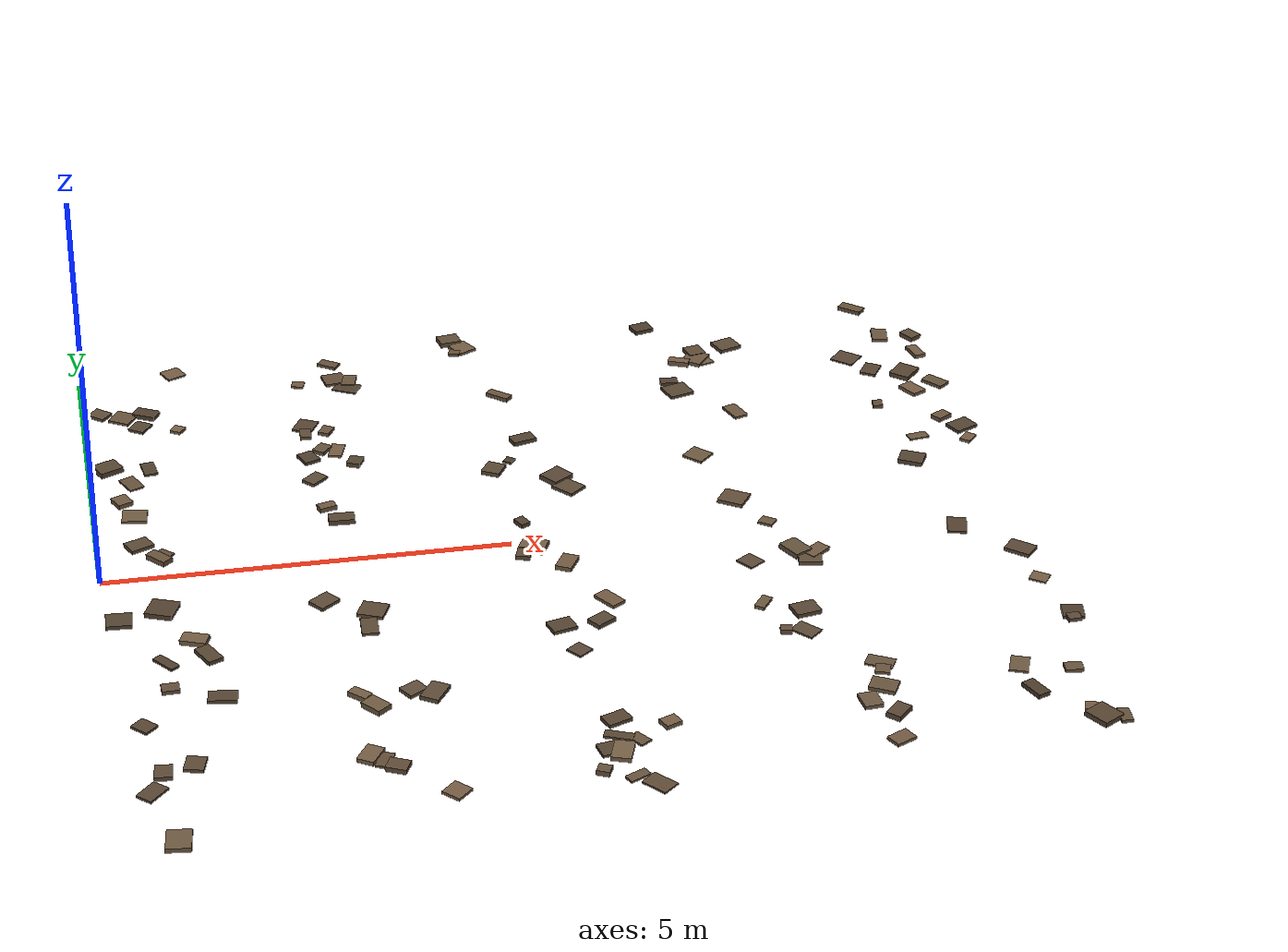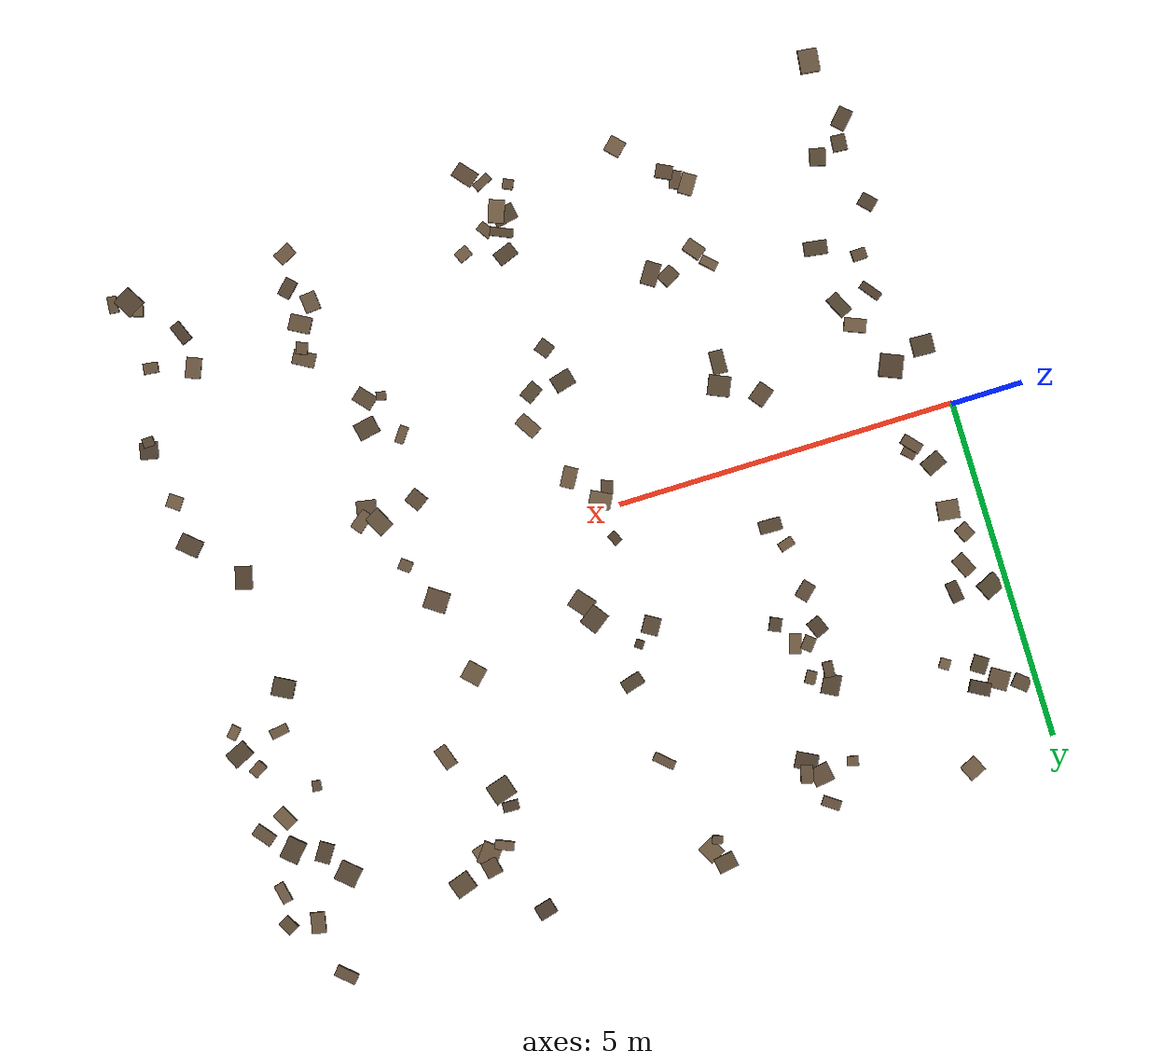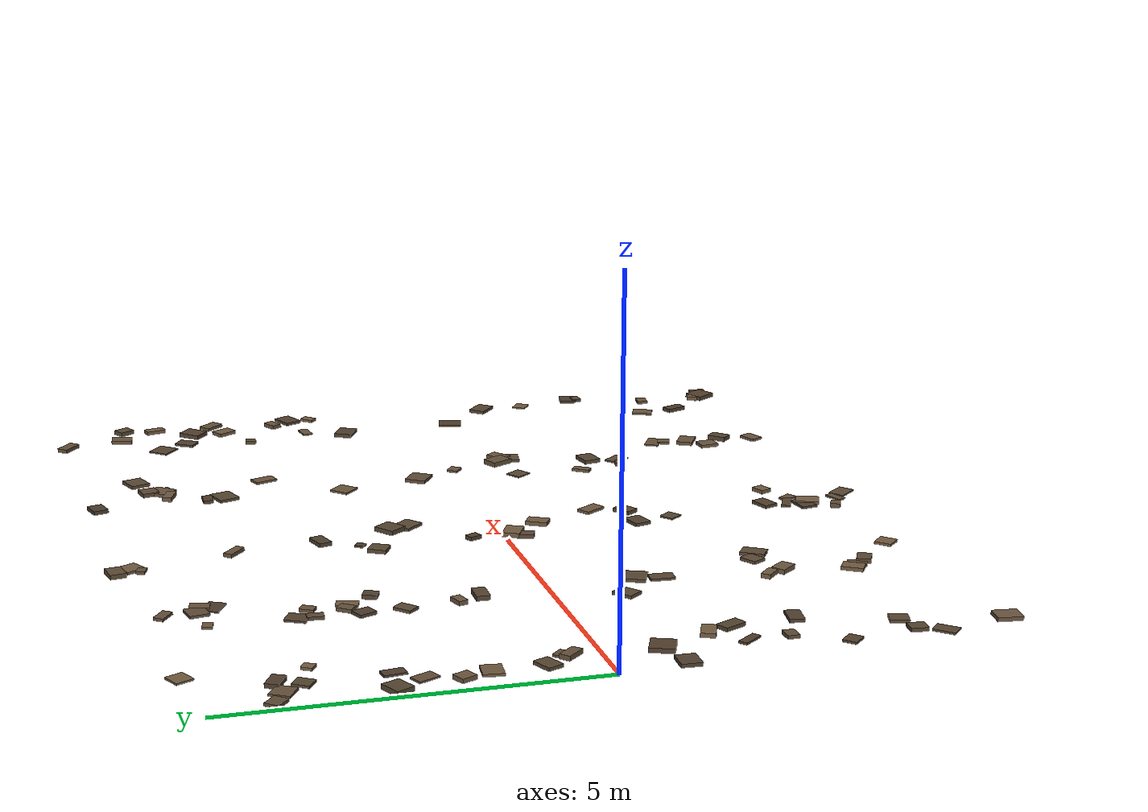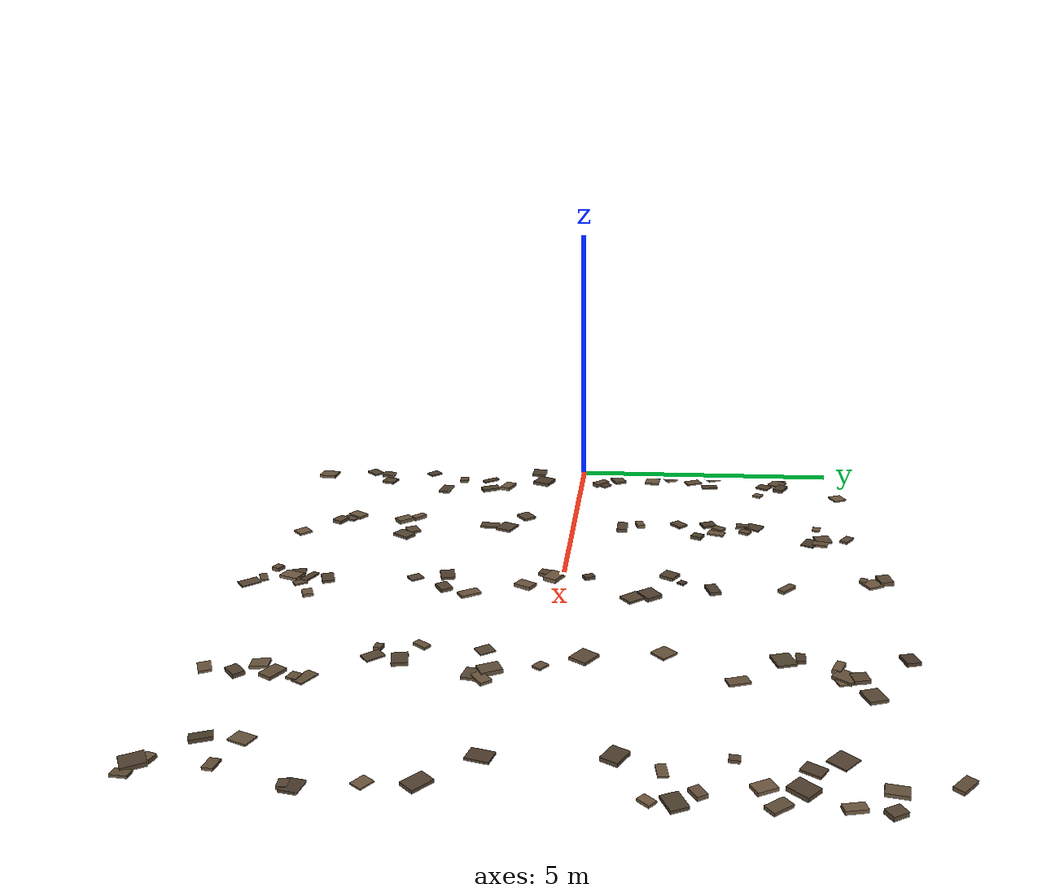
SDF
<?xml version="1.0"?>
<sdf version="1.6">
  <model name="dirt_track">
    <static>true</static>
    <link name="link">
      <visual name="clod_0"><pose>1.144 -1.835 0.0264 0 0 0.448</pose>
        <geometry><box><size>0.191 0.339 0.053</size></box></geometry>
        <material><ambient>0.23 0.18 0.13 1</ambient><diffuse>0.33 0.27 0.19 1</diffuse></material>
      </visual>
      <collision name="clod_0_c"><pose>1.144 -1.835 0.0264 0 0 1.658</pose>
        <geometry><box><size>0.191 0.339 0.053</size></box></geometry>
        <surface><friction><ode><mu>1.1</mu><mu2>1.1</mu2></ode></friction></surface>
      </collision>
      <visual name="clod_1"><pose>0.237 2.668 0.0349 0 0 0.444</pose>
        <geometry><box><size>0.312 0.262 0.070</size></box></geometry>
        <material><ambient>0.23 0.18 0.13 1</ambient><diffuse>0.33 0.27 0.19 1</diffuse></material>
      </visual>
      <collision name="clod_1_c"><pose>0.237 2.668 0.0349 0 0 1.989</pose>
        <geometry><box><size>0.312 0.262 0.070</size></box></geometry>
        <surface><friction><ode><mu>1.1</mu><mu2>1.1</mu2></ode></friction></surface>
      </collision>
      <visual name="clod_2"><pose>0.755 2.601 0.0152 0 0 0.138</pose>
        <geometry><box><size>0.172 0.301 0.030</size></box></geometry>
        <material><ambient>0.22 0.17 0.12 1</ambient><diffuse>0.31 0.25 0.18 1</diffuse></material>
      </visual>
      <collision name="clod_2_c"><pose>0.755 2.601 0.0152 0 0 2.645</pose>
        <geometry><box><size>0.172 0.301 0.030</size></box></geometry>
        <surface><friction><ode><mu>1.1</mu><mu2>1.1</mu2></ode></friction></surface>
      </collision>
      <visual name="clod_3"><pose>0.716 3.706 0.0177 0 0 2.548</pose>
        <geometry><box><size>0.221 0.242 0.035</size></box></geometry>
        <material><ambient>0.23 0.18 0.13 1</ambient><diffuse>0.33 0.27 0.19 1</diffuse></material>
      </visual>
      <collision name="clod_3_c"><pose>0.716 3.706 0.0177 0 0 0.981</pose>
        <geometry><box><size>0.221 0.242 0.035</size></box></geometry>
        <surface><friction><ode><mu>1.1</mu><mu2>1.1</mu2></ode></friction></surface>
      </collision>
      <visual name="clod_4"><pose>1.009 -1.490 0.0306 0 0 2.755</pose>
        <geometry><box><size>0.317 0.198 0.061</size></box></geometry>
        <material><ambient>0.31 0.25 0.18 1</ambient><diffuse>0.45 0.36 0.26 1</diffuse></material>
      </visual>
      <collision name="clod_4_c"><pose>1.009 -1.490 0.0306 0 0 2.374</pose>
        <geometry><box><size>0.317 0.198 0.061</size></box></geometry>
        <surface><friction><ode><mu>1.1</mu><mu2>1.1</mu2></ode></friction></surface>
      </collision>
      <visual name="clod_5"><pose>0.366 1.819 0.0296 0 0 0.425</pose>
        <geometry><box><size>0.200 0.223 0.059</size></box></geometry>
        <material><ambient>0.30 0.23 0.17 1</ambient><diffuse>0.43 0.34 0.25 1</diffuse></material>
      </visual>
      <collision name="clod_5_c"><pose>0.366 1.819 0.0296 0 0 2.729</pose>
        <geometry><box><size>0.200 0.223 0.059</size></box></geometry>
        <surface><friction><ode><mu>1.1</mu><mu2>1.1</mu2></ode></friction></surface>
      </collision>
      <visual name="clod_6"><pose>0.534 -5.323 0.0274 0 0 3.025</pose>
        <geometry><box><size>0.280 0.339 0.055</size></box></geometry>
        <material><ambient>0.30 0.23 0.17 1</ambient><diffuse>0.42 0.34 0.25 1</diffuse></material>
      </visual>
      <collision name="clod_6_c"><pose>0.534 -5.323 0.0274 0 0 2.872</pose>
        <geometry><box><size>0.280 0.339 0.055</size></box></geometry>
        <surface><friction><ode><mu>1.1</mu><mu2>1.1</mu2></ode></friction></surface>
      </collision>
      <visual name="clod_7"><pose>0.817 -3.964 0.0213 0 0 2.880</pose>
        <geometry><box><size>0.230 0.255 0.043</size></box></geometry>
        <material><ambient>0.25 0.19 0.14 1</ambient><diffuse>0.35 0.28 0.20 1</diffuse></material>
      </visual>
      <collision name="clod_7_c"><pose>0.817 -3.964 0.0213 0 0 1.857</pose>
        <geometry><box><size>0.230 0.255 0.043</size></box></geometry>
        <surface><friction><ode><mu>1.1</mu><mu2>1.1</mu2></ode></friction></surface>
      </collision>
      <visual name="clod_8"><pose>0.514 3.991 0.0163 0 0 1.013</pose>
        <geometry><box><size>0.280 0.289 0.033</size></box></geometry>
        <material><ambient>0.28 0.22 0.16 1</ambient><diffuse>0.40 0.32 0.23 1</diffuse></material>
      </visual>
      <collision name="clod_8_c"><pose>0.514 3.991 0.0163 0 0 2.051</pose>
        <geometry><box><size>0.280 0.289 0.033</size></box></geometry>
        <surface><friction><ode><mu>1.1</mu><mu2>1.1</mu2></ode></friction></surface>
      </collision>
      <visual name="clod_9"><pose>1.194 3.553 0.0195 0 0 2.572</pose>
        <geometry><box><size>0.150 0.153 0.039</size></box></geometry>
        <material><ambient>0.32 0.25 0.18 1</ambient><diffuse>0.46 0.37 0.27 1</diffuse></material>
      </visual>
      <collision name="clod_9_c"><pose>1.194 3.553 0.0195 0 0 0.543</pose>
        <geometry><box><size>0.150 0.153 0.039</size></box></geometry>
        <surface><friction><ode><mu>1.1</mu><mu2>1.1</mu2></ode></friction></surface>
      </collision>
      <visual name="clod_10"><pose>0.319 -4.395 0.0146 0 0 0.820</pose>
        <geometry><box><size>0.308 0.212 0.029</size></box></geometry>
        <material><ambient>0.24 0.19 0.13 1</ambient><diffuse>0.34 0.27 0.20 1</diffuse></material>
      </visual>
      <collision name="clod_10_c"><pose>0.319 -4.395 0.0146 0 0 2.777</pose>
        <geometry><box><size>0.308 0.212 0.029</size></box></geometry>
        <surface><friction><ode><mu>1.1</mu><mu2>1.1</mu2></ode></friction></surface>
      </collision>
      <visual name="clod_11"><pose>0.792 0.486 0.0160 0 0 0.794</pose>
        <geometry><box><size>0.157 0.200 0.032</size></box></geometry>
        <material><ambient>0.27 0.21 0.15 1</ambient><diffuse>0.38 0.30 0.22 1</diffuse></material>
      </visual>
      <collision name="clod_11_c"><pose>0.792 0.486 0.0160 0 0 2.351</pose>
        <geometry><box><size>0.157 0.200 0.032</size></box></geometry>
        <surface><friction><ode><mu>1.1</mu><mu2>1.1</mu2></ode></friction></surface>
      </collision>
      <visual name="clod_12"><pose>0.647 -1.900 0.0157 0 0 2.226</pose>
        <geometry><box><size>0.327 0.124 0.031</size></box></geometry>
        <material><ambient>0.22 0.17 0.13 1</ambient><diffuse>0.32 0.25 0.18 1</diffuse></material>
      </visual>
      <collision name="clod_12_c"><pose>0.647 -1.900 0.0157 0 0 2.475</pose>
        <geometry><box><size>0.327 0.124 0.031</size></box></geometry>
        <surface><friction><ode><mu>1.1</mu><mu2>1.1</mu2></ode></friction></surface>
      </collision>
      <visual name="clod_13"><pose>1.228 -2.719 0.0229 0 0 1.423</pose>
        <geometry><box><size>0.203 0.339 0.046</size></box></geometry>
        <material><ambient>0.22 0.18 0.13 1</ambient><diffuse>0.32 0.26 0.19 1</diffuse></material>
      </visual>
      <collision name="clod_13_c"><pose>1.228 -2.719 0.0229 0 0 3.030</pose>
        <geometry><box><size>0.203 0.339 0.046</size></box></geometry>
        <surface><friction><ode><mu>1.1</mu><mu2>1.1</mu2></ode></friction></surface>
      </collision>
      <visual name="clod_14"><pose>0.683 -0.778 0.0321 0 0 2.742</pose>
        <geometry><box><size>0.338 0.333 0.064</size></box></geometry>
        <material><ambient>0.22 0.17 0.13 1</ambient><diffuse>0.32 0.25 0.18 1</diffuse></material>
      </visual>
      <collision name="clod_14_c"><pose>0.683 -0.778 0.0321 0 0 1.160</pose>
        <geometry><box><size>0.338 0.333 0.064</size></box></geometry>
        <surface><friction><ode><mu>1.1</mu><mu2>1.1</mu2></ode></friction></surface>
      </collision>
      <visual name="clod_15"><pose>0.163 -0.930 0.0250 0 0 1.530</pose>
        <geometry><box><size>0.278 0.314 0.050</size></box></geometry>
        <material><ambient>0.22 0.18 0.13 1</ambient><diffuse>0.32 0.26 0.19 1</diffuse></material>
      </visual>
      <collision name="clod_15_c"><pose>0.163 -0.930 0.0250 0 0 0.546</pose>
        <geometry><box><size>0.278 0.314 0.050</size></box></geometry>
        <surface><friction><ode><mu>1.1</mu><mu2>1.1</mu2></ode></friction></surface>
      </collision>
      <visual name="clod_16"><pose>1.244 5.112 0.0127 0 0 0.428</pose>
        <geometry><box><size>0.263 0.254 0.025</size></box></geometry>
        <material><ambient>0.31 0.25 0.18 1</ambient><diffuse>0.45 0.36 0.26 1</diffuse></material>
      </visual>
      <collision name="clod_16_c"><pose>1.244 5.112 0.0127 0 0 1.125</pose>
        <geometry><box><size>0.263 0.254 0.025</size></box></geometry>
        <surface><friction><ode><mu>1.1</mu><mu2>1.1</mu2></ode></friction></surface>
      </collision>
      <visual name="clod_17"><pose>0.463 -4.067 0.0260 0 0 1.486</pose>
        <geometry><box><size>0.235 0.205 0.052</size></box></geometry>
        <material><ambient>0.24 0.19 0.14 1</ambient><diffuse>0.35 0.28 0.20 1</diffuse></material>
      </visual>
      <collision name="clod_17_c"><pose>0.463 -4.067 0.0260 0 0 2.152</pose>
        <geometry><box><size>0.235 0.205 0.052</size></box></geometry>
        <surface><friction><ode><mu>1.1</mu><mu2>1.1</mu2></ode></friction></surface>
      </collision>
      <visual name="clod_18"><pose>0.316 -3.137 0.0157 0 0 0.771</pose>
        <geometry><box><size>0.196 0.239 0.031</size></box></geometry>
        <material><ambient>0.23 0.18 0.13 1</ambient><diffuse>0.33 0.26 0.19 1</diffuse></material>
      </visual>
      <collision name="clod_18_c"><pose>0.316 -3.137 0.0157 0 0 2.664</pose>
        <geometry><box><size>0.196 0.239 0.031</size></box></geometry>
        <surface><friction><ode><mu>1.1</mu><mu2>1.1</mu2></ode></friction></surface>
      </collision>
      <visual name="clod_19"><pose>0.729 0.385 0.0339 0 0 0.721</pose>
        <geometry><box><size>0.153 0.303 0.068</size></box></geometry>
        <material><ambient>0.28 0.22 0.16 1</ambient><diffuse>0.40 0.32 0.23 1</diffuse></material>
      </visual>
      <collision name="clod_19_c"><pose>0.729 0.385 0.0339 0 0 3.089</pose>
        <geometry><box><size>0.153 0.303 0.068</size></box></geometry>
        <surface><friction><ode><mu>1.1</mu><mu2>1.1</mu2></ode></friction></surface>
      </collision>
      <visual name="clod_20"><pose>0.656 -2.446 0.0244 0 0 1.610</pose>
        <geometry><box><size>0.162 0.208 0.049</size></box></geometry>
        <material><ambient>0.27 0.21 0.15 1</ambient><diffuse>0.38 0.30 0.22 1</diffuse></material>
      </visual>
      <collision name="clod_20_c"><pose>0.656 -2.446 0.0244 0 0 2.455</pose>
        <geometry><box><size>0.162 0.208 0.049</size></box></geometry>
        <surface><friction><ode><mu>1.1</mu><mu2>1.1</mu2></ode></friction></surface>
      </collision>
      <visual name="clod_21"><pose>0.216 4.128 0.0204 0 0 2.442</pose>
        <geometry><box><size>0.247 0.205 0.041</size></box></geometry>
        <material><ambient>0.26 0.20 0.15 1</ambient><diffuse>0.37 0.30 0.22 1</diffuse></material>
      </visual>
      <collision name="clod_21_c"><pose>0.216 4.128 0.0204 0 0 1.482</pose>
        <geometry><box><size>0.247 0.205 0.041</size></box></geometry>
        <surface><friction><ode><mu>1.1</mu><mu2>1.1</mu2></ode></friction></surface>
      </collision>
      <visual name="clod_22"><pose>0.500 1.445 0.0186 0 0 1.453</pose>
        <geometry><box><size>0.274 0.310 0.037</size></box></geometry>
        <material><ambient>0.30 0.24 0.17 1</ambient><diffuse>0.43 0.35 0.25 1</diffuse></material>
      </visual>
      <collision name="clod_22_c"><pose>0.500 1.445 0.0186 0 0 1.131</pose>
        <geometry><box><size>0.274 0.310 0.037</size></box></geometry>
        <surface><friction><ode><mu>1.1</mu><mu2>1.1</mu2></ode></friction></surface>
      </collision>
      <visual name="clod_23"><pose>0.507 0.740 0.0233 0 0 1.986</pose>
        <geometry><box><size>0.229 0.303 0.047</size></box></geometry>
        <material><ambient>0.24 0.19 0.14 1</ambient><diffuse>0.35 0.28 0.20 1</diffuse></material>
      </visual>
      <collision name="clod_23_c"><pose>0.507 0.740 0.0233 0 0 0.822</pose>
        <geometry><box><size>0.229 0.303 0.047</size></box></geometry>
        <surface><friction><ode><mu>1.1</mu><mu2>1.1</mu2></ode></friction></surface>
      </collision>
      <visual name="clod_24"><pose>0.811 4.028 0.0304 0 0 2.640</pose>
        <geometry><box><size>0.308 0.189 0.061</size></box></geometry>
        <material><ambient>0.22 0.17 0.12 1</ambient><diffuse>0.31 0.25 0.18 1</diffuse></material>
      </visual>
      <collision name="clod_24_c"><pose>0.811 4.028 0.0304 0 0 3.041</pose>
        <geometry><box><size>0.308 0.189 0.061</size></box></geometry>
        <surface><friction><ode><mu>1.1</mu><mu2>1.1</mu2></ode></friction></surface>
      </collision>
      <visual name="clod_25"><pose>0.514 2.272 0.0127 0 0 2.000</pose>
        <geometry><box><size>0.310 0.199 0.025</size></box></geometry>
        <material><ambient>0.27 0.21 0.15 1</ambient><diffuse>0.39 0.31 0.22 1</diffuse></material>
      </visual>
      <collision name="clod_25_c"><pose>0.514 2.272 0.0127 0 0 0.157</pose>
        <geometry><box><size>0.310 0.199 0.025</size></box></geometry>
        <surface><friction><ode><mu>1.1</mu><mu2>1.1</mu2></ode></friction></surface>
      </collision>
      <visual name="clod_26"><pose>3.362 2.296 0.0306 0 0 1.139</pose>
        <geometry><box><size>0.196 0.175 0.061</size></box></geometry>
        <material><ambient>0.22 0.18 0.13 1</ambient><diffuse>0.32 0.26 0.19 1</diffuse></material>
      </visual>
      <collision name="clod_26_c"><pose>3.362 2.296 0.0306 0 0 1.828</pose>
        <geometry><box><size>0.196 0.175 0.061</size></box></geometry>
        <surface><friction><ode><mu>1.1</mu><mu2>1.1</mu2></ode></friction></surface>
      </collision>
      <visual name="clod_27"><pose>3.561 -4.962 0.0182 0 0 0.768</pose>
        <geometry><box><size>0.242 0.240 0.036</size></box></geometry>
        <material><ambient>0.32 0.25 0.18 1</ambient><diffuse>0.46 0.36 0.26 1</diffuse></material>
      </visual>
      <collision name="clod_27_c"><pose>3.561 -4.962 0.0182 0 0 0.176</pose>
        <geometry><box><size>0.242 0.240 0.036</size></box></geometry>
        <surface><friction><ode><mu>1.1</mu><mu2>1.1</mu2></ode></friction></surface>
      </collision>
      <visual name="clod_28"><pose>3.167 2.645 0.0152 0 0 1.267</pose>
        <geometry><box><size>0.300 0.175 0.030</size></box></geometry>
        <material><ambient>0.32 0.25 0.18 1</ambient><diffuse>0.45 0.36 0.26 1</diffuse></material>
      </visual>
      <collision name="clod_28_c"><pose>3.167 2.645 0.0152 0 0 0.889</pose>
        <geometry><box><size>0.300 0.175 0.030</size></box></geometry>
        <surface><friction><ode><mu>1.1</mu><mu2>1.1</mu2></ode></friction></surface>
      </collision>
      <visual name="clod_29"><pose>3.603 -3.058 0.0265 0 0 0.988</pose>
        <geometry><box><size>0.338 0.230 0.053</size></box></geometry>
        <material><ambient>0.25 0.20 0.15 1</ambient><diffuse>0.36 0.29 0.21 1</diffuse></material>
      </visual>
      <collision name="clod_29_c"><pose>3.603 -3.058 0.0265 0 0 0.448</pose>
        <geometry><box><size>0.338 0.230 0.053</size></box></geometry>
        <surface><friction><ode><mu>1.1</mu><mu2>1.1</mu2></ode></friction></surface>
      </collision>
      <visual name="clod_30"><pose>3.371 -2.953 0.0218 0 0 2.096</pose>
        <geometry><box><size>0.214 0.258 0.044</size></box></geometry>
        <material><ambient>0.26 0.21 0.15 1</ambient><diffuse>0.37 0.30 0.22 1</diffuse></material>
      </visual>
      <collision name="clod_30_c"><pose>3.371 -2.953 0.0218 0 0 0.812</pose>
        <geometry><box><size>0.214 0.258 0.044</size></box></geometry>
        <surface><friction><ode><mu>1.1</mu><mu2>1.1</mu2></ode></friction></surface>
      </collision>
      <visual name="clod_31"><pose>2.726 -4.140 0.0260 0 0 1.005</pose>
        <geometry><box><size>0.303 0.210 0.052</size></box></geometry>
        <material><ambient>0.31 0.25 0.18 1</ambient><diffuse>0.45 0.36 0.26 1</diffuse></material>
      </visual>
      <collision name="clod_31_c"><pose>2.726 -4.140 0.0260 0 0 1.901</pose>
        <geometry><box><size>0.303 0.210 0.052</size></box></geometry>
        <surface><friction><ode><mu>1.1</mu><mu2>1.1</mu2></ode></friction></surface>
      </collision>
      <visual name="clod_32"><pose>2.759 -2.963 0.0321 0 0 0.796</pose>
        <geometry><box><size>0.135 0.255 0.064</size></box></geometry>
        <material><ambient>0.31 0.25 0.18 1</ambient><diffuse>0.45 0.36 0.26 1</diffuse></material>
      </visual>
      <collision name="clod_32_c"><pose>2.759 -2.963 0.0321 0 0 1.873</pose>
        <geometry><box><size>0.135 0.255 0.064</size></box></geometry>
        <surface><friction><ode><mu>1.1</mu><mu2>1.1</mu2></ode></friction></surface>
      </collision>
      <visual name="clod_33"><pose>3.357 4.558 0.0186 0 0 0.158</pose>
        <geometry><box><size>0.285 0.276 0.037</size></box></geometry>
        <material><ambient>0.26 0.21 0.15 1</ambient><diffuse>0.38 0.30 0.22 1</diffuse></material>
      </visual>
      <collision name="clod_33_c"><pose>3.357 4.558 0.0186 0 0 0.723</pose>
        <geometry><box><size>0.285 0.276 0.037</size></box></geometry>
        <surface><friction><ode><mu>1.1</mu><mu2>1.1</mu2></ode></friction></surface>
      </collision>
      <visual name="clod_34"><pose>2.842 3.358 0.0142 0 0 1.079</pose>
        <geometry><box><size>0.297 0.259 0.028</size></box></geometry>
        <material><ambient>0.23 0.18 0.13 1</ambient><diffuse>0.33 0.26 0.19 1</diffuse></material>
      </visual>
      <collision name="clod_34_c"><pose>2.842 3.358 0.0142 0 0 0.371</pose>
        <geometry><box><size>0.297 0.259 0.028</size></box></geometry>
        <surface><friction><ode><mu>1.1</mu><mu2>1.1</mu2></ode></friction></surface>
      </collision>
      <visual name="clod_35"><pose>3.506 4.316 0.0102 0 0 2.652</pose>
        <geometry><box><size>0.331 0.238 0.020</size></box></geometry>
        <material><ambient>0.21 0.17 0.12 1</ambient><diffuse>0.31 0.25 0.18 1</diffuse></material>
      </visual>
      <collision name="clod_35_c"><pose>3.506 4.316 0.0102 0 0 0.982</pose>
        <geometry><box><size>0.331 0.238 0.020</size></box></geometry>
        <surface><friction><ode><mu>1.1</mu><mu2>1.1</mu2></ode></friction></surface>
      </collision>
      <visual name="clod_36"><pose>2.869 -4.252 0.0146 0 0 2.775</pose>
        <geometry><box><size>0.167 0.266 0.029</size></box></geometry>
        <material><ambient>0.26 0.21 0.15 1</ambient><diffuse>0.38 0.30 0.22 1</diffuse></material>
      </visual>
      <collision name="clod_36_c"><pose>2.869 -4.252 0.0146 0 0 1.047</pose>
        <geometry><box><size>0.167 0.266 0.029</size></box></geometry>
        <surface><friction><ode><mu>1.1</mu><mu2>1.1</mu2></ode></friction></surface>
      </collision>
      <visual name="clod_37"><pose>2.873 1.237 0.0308 0 0 1.854</pose>
        <geometry><box><size>0.134 0.220 0.062</size></box></geometry>
        <material><ambient>0.30 0.24 0.17 1</ambient><diffuse>0.43 0.34 0.25 1</diffuse></material>
      </visual>
      <collision name="clod_37_c"><pose>2.873 1.237 0.0308 0 0 0.528</pose>
        <geometry><box><size>0.134 0.220 0.062</size></box></geometry>
        <surface><friction><ode><mu>1.1</mu><mu2>1.1</mu2></ode></friction></surface>
      </collision>
      <visual name="clod_38"><pose>3.019 0.914 0.0329 0 0 3.114</pose>
        <geometry><box><size>0.325 0.187 0.066</size></box></geometry>
        <material><ambient>0.24 0.19 0.13 1</ambient><diffuse>0.34 0.27 0.20 1</diffuse></material>
      </visual>
      <collision name="clod_38_c"><pose>3.019 0.914 0.0329 0 0 2.188</pose>
        <geometry><box><size>0.325 0.187 0.066</size></box></geometry>
        <surface><friction><ode><mu>1.1</mu><mu2>1.1</mu2></ode></friction></surface>
      </collision>
      <visual name="clod_39"><pose>2.867 4.502 0.0144 0 0 1.323</pose>
        <geometry><box><size>0.137 0.163 0.029</size></box></geometry>
        <material><ambient>0.30 0.23 0.17 1</ambient><diffuse>0.43 0.34 0.25 1</diffuse></material>
      </visual>
      <collision name="clod_39_c"><pose>2.867 4.502 0.0144 0 0 1.558</pose>
        <geometry><box><size>0.137 0.163 0.029</size></box></geometry>
        <surface><friction><ode><mu>1.1</mu><mu2>1.1</mu2></ode></friction></surface>
      </collision>
      <visual name="clod_40"><pose>3.556 4.490 0.0200 0 0 1.322</pose>
        <geometry><box><size>0.264 0.179 0.040</size></box></geometry>
        <material><ambient>0.28 0.22 0.16 1</ambient><diffuse>0.40 0.32 0.23 1</diffuse></material>
      </visual>
      <collision name="clod_40_c"><pose>3.556 4.490 0.0200 0 0 1.476</pose>
        <geometry><box><size>0.264 0.179 0.040</size></box></geometry>
        <surface><friction><ode><mu>1.1</mu><mu2>1.1</mu2></ode></friction></surface>
      </collision>
      <visual name="clod_41"><pose>3.048 -1.559 0.0168 0 0 3.093</pose>
        <geometry><box><size>0.203 0.336 0.034</size></box></geometry>
        <material><ambient>0.24 0.19 0.14 1</ambient><diffuse>0.35 0.28 0.20 1</diffuse></material>
      </visual>
      <collision name="clod_41_c"><pose>3.048 -1.559 0.0168 0 0 2.734</pose>
        <geometry><box><size>0.203 0.336 0.034</size></box></geometry>
        <surface><friction><ode><mu>1.1</mu><mu2>1.1</mu2></ode></friction></surface>
      </collision>
      <visual name="clod_42"><pose>3.133 -1.228 0.0231 0 0 1.157</pose>
        <geometry><box><size>0.295 0.321 0.046</size></box></geometry>
        <material><ambient>0.25 0.19 0.14 1</ambient><diffuse>0.35 0.28 0.20 1</diffuse></material>
      </visual>
      <collision name="clod_42_c"><pose>3.133 -1.228 0.0231 0 0 1.044</pose>
        <geometry><box><size>0.295 0.321 0.046</size></box></geometry>
        <surface><friction><ode><mu>1.1</mu><mu2>1.1</mu2></ode></friction></surface>
      </collision>
      <visual name="clod_43"><pose>2.986 2.697 0.0260 0 0 0.897</pose>
        <geometry><box><size>0.212 0.166 0.052</size></box></geometry>
        <material><ambient>0.28 0.22 0.16 1</ambient><diffuse>0.39 0.32 0.23 1</diffuse></material>
      </visual>
      <collision name="clod_43_c"><pose>2.986 2.697 0.0260 0 0 0.992</pose>
        <geometry><box><size>0.212 0.166 0.052</size></box></geometry>
        <surface><friction><ode><mu>1.1</mu><mu2>1.1</mu2></ode></friction></surface>
      </collision>
      <visual name="clod_44"><pose>2.789 2.507 0.0226 0 0 0.380</pose>
        <geometry><box><size>0.208 0.252 0.045</size></box></geometry>
        <material><ambient>0.21 0.17 0.12 1</ambient><diffuse>0.31 0.25 0.18 1</diffuse></material>
      </visual>
      <collision name="clod_44_c"><pose>2.789 2.507 0.0226 0 0 1.185</pose>
        <geometry><box><size>0.208 0.252 0.045</size></box></geometry>
        <surface><friction><ode><mu>1.1</mu><mu2>1.1</mu2></ode></friction></surface>
      </collision>
      <visual name="clod_45"><pose>2.590 -0.931 0.0226 0 0 0.655</pose>
        <geometry><box><size>0.295 0.240 0.045</size></box></geometry>
        <material><ambient>0.25 0.20 0.14 1</ambient><diffuse>0.36 0.29 0.21 1</diffuse></material>
      </visual>
      <collision name="clod_45_c"><pose>2.590 -0.931 0.0226 0 0 2.815</pose>
        <geometry><box><size>0.295 0.240 0.045</size></box></geometry>
        <surface><friction><ode><mu>1.1</mu><mu2>1.1</mu2></ode></friction></surface>
      </collision>
      <visual name="clod_46"><pose>2.807 1.960 0.0203 0 0 0.739</pose>
        <geometry><box><size>0.264 0.197 0.041</size></box></geometry>
        <material><ambient>0.25 0.20 0.14 1</ambient><diffuse>0.36 0.29 0.21 1</diffuse></material>
      </visual>
      <collision name="clod_46_c"><pose>2.807 1.960 0.0203 0 0 2.680</pose>
        <geometry><box><size>0.264 0.197 0.041</size></box></geometry>
        <surface><friction><ode><mu>1.1</mu><mu2>1.1</mu2></ode></friction></surface>
      </collision>
      <visual name="clod_47"><pose>2.818 3.136 0.0228 0 0 3.066</pose>
        <geometry><box><size>0.146 0.225 0.046</size></box></geometry>
        <material><ambient>0.25 0.20 0.15 1</ambient><diffuse>0.36 0.29 0.21 1</diffuse></material>
      </visual>
      <collision name="clod_47_c"><pose>2.818 3.136 0.0228 0 0 2.917</pose>
        <geometry><box><size>0.146 0.225 0.046</size></box></geometry>
        <surface><friction><ode><mu>1.1</mu><mu2>1.1</mu2></ode></friction></surface>
      </collision>
      <visual name="clod_48"><pose>2.994 -4.406 0.0312 0 0 2.690</pose>
        <geometry><box><size>0.246 0.197 0.062</size></box></geometry>
        <material><ambient>0.26 0.20 0.15 1</ambient><diffuse>0.37 0.29 0.21 1</diffuse></material>
      </visual>
      <collision name="clod_48_c"><pose>2.994 -4.406 0.0312 0 0 2.375</pose>
        <geometry><box><size>0.246 0.197 0.062</size></box></geometry>
        <surface><friction><ode><mu>1.1</mu><mu2>1.1</mu2></ode></friction></surface>
      </collision>
      <visual name="clod_49"><pose>2.907 -3.213 0.0339 0 0 2.239</pose>
        <geometry><box><size>0.284 0.201 0.068</size></box></geometry>
        <material><ambient>0.30 0.24 0.17 1</ambient><diffuse>0.43 0.35 0.25 1</diffuse></material>
      </visual>
      <collision name="clod_49_c"><pose>2.907 -3.213 0.0339 0 0 0.886</pose>
        <geometry><box><size>0.284 0.201 0.068</size></box></geometry>
        <surface><friction><ode><mu>1.1</mu><mu2>1.1</mu2></ode></friction></surface>
      </collision>
      <visual name="clod_50"><pose>3.095 3.174 0.0231 0 0 2.610</pose>
        <geometry><box><size>0.150 0.194 0.046</size></box></geometry>
        <material><ambient>0.28 0.22 0.16 1</ambient><diffuse>0.40 0.32 0.23 1</diffuse></material>
      </visual>
      <collision name="clod_50_c"><pose>3.095 3.174 0.0231 0 0 2.762</pose>
        <geometry><box><size>0.150 0.194 0.046</size></box></geometry>
        <surface><friction><ode><mu>1.1</mu><mu2>1.1</mu2></ode></friction></surface>
      </collision>
      <visual name="clod_51"><pose>3.339 4.992 0.0207 0 0 0.951</pose>
        <geometry><box><size>0.144 0.271 0.041</size></box></geometry>
        <material><ambient>0.27 0.22 0.16 1</ambient><diffuse>0.39 0.31 0.23 1</diffuse></material>
      </visual>
      <collision name="clod_51_c"><pose>3.339 4.992 0.0207 0 0 2.284</pose>
        <geometry><box><size>0.144 0.271 0.041</size></box></geometry>
        <surface><friction><ode><mu>1.1</mu><mu2>1.1</mu2></ode></friction></surface>
      </collision>
      <visual name="clod_52"><pose>5.208 0.434 0.0275 0 0 2.008</pose>
        <geometry><box><size>0.177 0.132 0.055</size></box></geometry>
        <material><ambient>0.22 0.18 0.13 1</ambient><diffuse>0.32 0.25 0.18 1</diffuse></material>
      </visual>
      <collision name="clod_52_c"><pose>5.208 0.434 0.0275 0 0 2.543</pose>
        <geometry><box><size>0.177 0.132 0.055</size></box></geometry>
        <surface><friction><ode><mu>1.1</mu><mu2>1.1</mu2></ode></friction></surface>
      </collision>
      <visual name="clod_53"><pose>5.314 1.996 0.0145 0 0 2.536</pose>
        <geometry><box><size>0.122 0.126 0.029</size></box></geometry>
        <material><ambient>0.21 0.17 0.12 1</ambient><diffuse>0.30 0.24 0.17 1</diffuse></material>
      </visual>
      <collision name="clod_53_c"><pose>5.314 1.996 0.0145 0 0 0.693</pose>
        <geometry><box><size>0.122 0.126 0.029</size></box></geometry>
        <surface><friction><ode><mu>1.1</mu><mu2>1.1</mu2></ode></friction></surface>
      </collision>
      <visual name="clod_54"><pose>5.041 5.365 0.0330 0 0 1.726</pose>
        <geometry><box><size>0.227 0.285 0.066</size></box></geometry>
        <material><ambient>0.26 0.20 0.15 1</ambient><diffuse>0.37 0.30 0.21 1</diffuse></material>
      </visual>
      <collision name="clod_54_c"><pose>5.041 5.365 0.0330 0 0 1.103</pose>
        <geometry><box><size>0.227 0.285 0.066</size></box></geometry>
        <surface><friction><ode><mu>1.1</mu><mu2>1.1</mu2></ode></friction></surface>
      </collision>
      <visual name="clod_55"><pose>5.540 -5.029 0.0130 0 0 2.009</pose>
        <geometry><box><size>0.125 0.266 0.026</size></box></geometry>
        <material><ambient>0.28 0.22 0.16 1</ambient><diffuse>0.40 0.32 0.23 1</diffuse></material>
      </visual>
      <collision name="clod_55_c"><pose>5.540 -5.029 0.0130 0 0 0.125</pose>
        <geometry><box><size>0.125 0.266 0.026</size></box></geometry>
        <surface><friction><ode><mu>1.1</mu><mu2>1.1</mu2></ode></friction></surface>
      </collision>
      <visual name="clod_56"><pose>5.466 -4.567 0.0264 0 0 2.797</pose>
        <geometry><box><size>0.232 0.335 0.053</size></box></geometry>
        <material><ambient>0.32 0.25 0.18 1</ambient><diffuse>0.46 0.37 0.27 1</diffuse></material>
      </visual>
      <collision name="clod_56_c"><pose>5.466 -4.567 0.0264 0 0 1.797</pose>
        <geometry><box><size>0.232 0.335 0.053</size></box></geometry>
        <surface><friction><ode><mu>1.1</mu><mu2>1.1</mu2></ode></friction></surface>
      </collision>
      <visual name="clod_57"><pose>5.375 -4.482 0.0171 0 0 0.175</pose>
        <geometry><box><size>0.334 0.235 0.034</size></box></geometry>
        <material><ambient>0.23 0.18 0.13 1</ambient><diffuse>0.32 0.26 0.19 1</diffuse></material>
      </visual>
      <collision name="clod_57_c"><pose>5.375 -4.482 0.0171 0 0 2.263</pose>
        <geometry><box><size>0.334 0.235 0.034</size></box></geometry>
        <surface><friction><ode><mu>1.1</mu><mu2>1.1</mu2></ode></friction></surface>
      </collision>
      <visual name="clod_58"><pose>5.746 -5.205 0.0115 0 0 2.265</pose>
        <geometry><box><size>0.324 0.229 0.023</size></box></geometry>
        <material><ambient>0.26 0.20 0.15 1</ambient><diffuse>0.37 0.29 0.21 1</diffuse></material>
      </visual>
      <collision name="clod_58_c"><pose>5.746 -5.205 0.0115 0 0 0.264</pose>
        <geometry><box><size>0.324 0.229 0.023</size></box></geometry>
        <surface><friction><ode><mu>1.1</mu><mu2>1.1</mu2></ode></friction></surface>
      </collision>
      <visual name="clod_59"><pose>5.194 -4.891 0.0325 0 0 1.126</pose>
        <geometry><box><size>0.142 0.153 0.065</size></box></geometry>
        <material><ambient>0.27 0.22 0.16 1</ambient><diffuse>0.39 0.31 0.23 1</diffuse></material>
      </visual>
      <collision name="clod_59_c"><pose>5.194 -4.891 0.0325 0 0 3.138</pose>
        <geometry><box><size>0.142 0.153 0.065</size></box></geometry>
        <surface><friction><ode><mu>1.1</mu><mu2>1.1</mu2></ode></friction></surface>
      </collision>
      <visual name="clod_60"><pose>5.190 5.142 0.0193 0 0 0.492</pose>
        <geometry><box><size>0.258 0.284 0.039</size></box></geometry>
        <material><ambient>0.31 0.25 0.18 1</ambient><diffuse>0.45 0.36 0.26 1</diffuse></material>
      </visual>
      <collision name="clod_60_c"><pose>5.190 5.142 0.0193 0 0 1.279</pose>
        <geometry><box><size>0.258 0.284 0.039</size></box></geometry>
        <surface><friction><ode><mu>1.1</mu><mu2>1.1</mu2></ode></friction></surface>
      </collision>
      <visual name="clod_61"><pose>6.101 -4.113 0.0268 0 0 1.967</pose>
        <geometry><box><size>0.168 0.205 0.054</size></box></geometry>
        <material><ambient>0.32 0.25 0.18 1</ambient><diffuse>0.45 0.36 0.26 1</diffuse></material>
      </visual>
      <collision name="clod_61_c"><pose>6.101 -4.113 0.0268 0 0 0.913</pose>
        <geometry><box><size>0.168 0.205 0.054</size></box></geometry>
        <surface><friction><ode><mu>1.1</mu><mu2>1.1</mu2></ode></friction></surface>
      </collision>
      <visual name="clod_62"><pose>5.571 2.494 0.0281 0 0 0.278</pose>
        <geometry><box><size>0.309 0.186 0.056</size></box></geometry>
        <material><ambient>0.22 0.18 0.13 1</ambient><diffuse>0.32 0.26 0.19 1</diffuse></material>
      </visual>
      <collision name="clod_62_c"><pose>5.571 2.494 0.0281 0 0 1.670</pose>
        <geometry><box><size>0.309 0.186 0.056</size></box></geometry>
        <surface><friction><ode><mu>1.1</mu><mu2>1.1</mu2></ode></friction></surface>
      </collision>
      <visual name="clod_63"><pose>5.747 -1.927 0.0281 0 0 2.141</pose>
        <geometry><box><size>0.200 0.269 0.056</size></box></geometry>
        <material><ambient>0.24 0.19 0.14 1</ambient><diffuse>0.34 0.28 0.20 1</diffuse></material>
      </visual>
      <collision name="clod_63_c"><pose>5.747 -1.927 0.0281 0 0 1.952</pose>
        <geometry><box><size>0.200 0.269 0.056</size></box></geometry>
        <surface><friction><ode><mu>1.1</mu><mu2>1.1</mu2></ode></friction></surface>
      </collision>
      <visual name="clod_64"><pose>5.252 -0.149 0.0345 0 0 2.660</pose>
        <geometry><box><size>0.318 0.247 0.069</size></box></geometry>
        <material><ambient>0.31 0.24 0.18 1</ambient><diffuse>0.45 0.36 0.26 1</diffuse></material>
      </visual>
      <collision name="clod_64_c"><pose>5.252 -0.149 0.0345 0 0 1.065</pose>
        <geometry><box><size>0.318 0.247 0.069</size></box></geometry>
        <surface><friction><ode><mu>1.1</mu><mu2>1.1</mu2></ode></friction></surface>
      </collision>
      <visual name="clod_65"><pose>5.934 1.191 0.0212 0 0 0.698</pose>
        <geometry><box><size>0.272 0.327 0.042</size></box></geometry>
        <material><ambient>0.25 0.20 0.14 1</ambient><diffuse>0.36 0.29 0.21 1</diffuse></material>
      </visual>
      <collision name="clod_65_c"><pose>5.934 1.191 0.0212 0 0 1.374</pose>
        <geometry><box><size>0.272 0.327 0.042</size></box></geometry>
        <surface><friction><ode><mu>1.1</mu><mu2>1.1</mu2></ode></friction></surface>
      </collision>
      <visual name="clod_66"><pose>5.584 -0.597 0.0295 0 0 1.052</pose>
        <geometry><box><size>0.305 0.204 0.059</size></box></geometry>
        <material><ambient>0.31 0.24 0.17 1</ambient><diffuse>0.44 0.35 0.25 1</diffuse></material>
      </visual>
      <collision name="clod_66_c"><pose>5.584 -0.597 0.0295 0 0 2.237</pose>
        <geometry><box><size>0.305 0.204 0.059</size></box></geometry>
        <surface><friction><ode><mu>1.1</mu><mu2>1.1</mu2></ode></friction></surface>
      </collision>
      <visual name="clod_67"><pose>5.830 1.460 0.0330 0 0 2.199</pose>
        <geometry><box><size>0.282 0.317 0.066</size></box></geometry>
        <material><ambient>0.24 0.19 0.14 1</ambient><diffuse>0.34 0.27 0.20 1</diffuse></material>
      </visual>
      <collision name="clod_67_c"><pose>5.830 1.460 0.0330 0 0 1.625</pose>
        <geometry><box><size>0.282 0.317 0.066</size></box></geometry>
        <surface><friction><ode><mu>1.1</mu><mu2>1.1</mu2></ode></friction></surface>
      </collision>
      <visual name="clod_68"><pose>5.696 -4.358 0.0136 0 0 2.167</pose>
        <geometry><box><size>0.222 0.152 0.027</size></box></geometry>
        <material><ambient>0.28 0.22 0.16 1</ambient><diffuse>0.40 0.32 0.23 1</diffuse></material>
      </visual>
      <collision name="clod_68_c"><pose>5.696 -4.358 0.0136 0 0 2.826</pose>
        <geometry><box><size>0.222 0.152 0.027</size></box></geometry>
        <surface><friction><ode><mu>1.1</mu><mu2>1.1</mu2></ode></friction></surface>
      </collision>
      <visual name="clod_69"><pose>5.264 -1.953 0.0227 0 0 1.831</pose>
        <geometry><box><size>0.239 0.304 0.045</size></box></geometry>
        <material><ambient>0.23 0.18 0.13 1</ambient><diffuse>0.32 0.26 0.19 1</diffuse></material>
      </visual>
      <collision name="clod_69_c"><pose>5.264 -1.953 0.0227 0 0 0.970</pose>
        <geometry><box><size>0.239 0.304 0.045</size></box></geometry>
        <surface><friction><ode><mu>1.1</mu><mu2>1.1</mu2></ode></friction></surface>
      </collision>
      <visual name="clod_70"><pose>5.065 5.017 0.0206 0 0 1.202</pose>
        <geometry><box><size>0.121 0.152 0.041</size></box></geometry>
        <material><ambient>0.27 0.21 0.15 1</ambient><diffuse>0.39 0.31 0.22 1</diffuse></material>
      </visual>
      <collision name="clod_70_c"><pose>5.065 5.017 0.0206 0 0 2.704</pose>
        <geometry><box><size>0.121 0.152 0.041</size></box></geometry>
        <surface><friction><ode><mu>1.1</mu><mu2>1.1</mu2></ode></friction></surface>
      </collision>
      <visual name="clod_71"><pose>5.483 -4.259 0.0163 0 0 1.154</pose>
        <geometry><box><size>0.128 0.338 0.033</size></box></geometry>
        <material><ambient>0.24 0.18 0.13 1</ambient><diffuse>0.34 0.27 0.19 1</diffuse></material>
      </visual>
      <collision name="clod_71_c"><pose>5.483 -4.259 0.0163 0 0 0.186</pose>
        <geometry><box><size>0.128 0.338 0.033</size></box></geometry>
        <surface><friction><ode><mu>1.1</mu><mu2>1.1</mu2></ode></friction></surface>
      </collision>
      <visual name="clod_72"><pose>5.075 1.788 0.0273 0 0 1.031</pose>
        <geometry><box><size>0.258 0.241 0.055</size></box></geometry>
        <material><ambient>0.24 0.19 0.14 1</ambient><diffuse>0.35 0.28 0.20 1</diffuse></material>
      </visual>
      <collision name="clod_72_c"><pose>5.075 1.788 0.0273 0 0 1.873</pose>
        <geometry><box><size>0.258 0.241 0.055</size></box></geometry>
        <surface><friction><ode><mu>1.1</mu><mu2>1.1</mu2></ode></friction></surface>
      </collision>
      <visual name="clod_73"><pose>5.379 -2.481 0.0115 0 0 0.637</pose>
        <geometry><box><size>0.209 0.220 0.023</size></box></geometry>
        <material><ambient>0.25 0.20 0.14 1</ambient><diffuse>0.35 0.28 0.21 1</diffuse></material>
      </visual>
      <collision name="clod_73_c"><pose>5.379 -2.481 0.0115 0 0 0.814</pose>
        <geometry><box><size>0.209 0.220 0.023</size></box></geometry>
        <surface><friction><ode><mu>1.1</mu><mu2>1.1</mu2></ode></friction></surface>
      </collision>
      <visual name="clod_74"><pose>5.932 -1.479 0.0205 0 0 0.559</pose>
        <geometry><box><size>0.197 0.336 0.041</size></box></geometry>
        <material><ambient>0.31 0.24 0.17 1</ambient><diffuse>0.44 0.35 0.25 1</diffuse></material>
      </visual>
      <collision name="clod_74_c"><pose>5.932 -1.479 0.0205 0 0 0.724</pose>
        <geometry><box><size>0.197 0.336 0.041</size></box></geometry>
        <surface><friction><ode><mu>1.1</mu><mu2>1.1</mu2></ode></friction></surface>
      </collision>
      <visual name="clod_75"><pose>5.519 -3.938 0.0229 0 0 1.930</pose>
        <geometry><box><size>0.206 0.302 0.046</size></box></geometry>
        <material><ambient>0.23 0.18 0.13 1</ambient><diffuse>0.33 0.26 0.19 1</diffuse></material>
      </visual>
      <collision name="clod_75_c"><pose>5.519 -3.938 0.0229 0 0 1.197</pose>
        <geometry><box><size>0.206 0.302 0.046</size></box></geometry>
        <surface><friction><ode><mu>1.1</mu><mu2>1.1</mu2></ode></friction></surface>
      </collision>
      <visual name="clod_76"><pose>5.104 -0.301 0.0282 0 0 1.260</pose>
        <geometry><box><size>0.209 0.176 0.056</size></box></geometry>
        <material><ambient>0.25 0.20 0.14 1</ambient><diffuse>0.36 0.28 0.21 1</diffuse></material>
      </visual>
      <collision name="clod_76_c"><pose>5.104 -0.301 0.0282 0 0 1.854</pose>
        <geometry><box><size>0.209 0.176 0.056</size></box></geometry>
        <surface><friction><ode><mu>1.1</mu><mu2>1.1</mu2></ode></friction></surface>
      </collision>
      <visual name="clod_77"><pose>5.463 3.707 0.0275 0 0 0.835</pose>
        <geometry><box><size>0.127 0.327 0.055</size></box></geometry>
        <material><ambient>0.28 0.22 0.16 1</ambient><diffuse>0.40 0.32 0.23 1</diffuse></material>
      </visual>
      <collision name="clod_77_c"><pose>5.463 3.707 0.0275 0 0 1.310</pose>
        <geometry><box><size>0.127 0.327 0.055</size></box></geometry>
        <surface><friction><ode><mu>1.1</mu><mu2>1.1</mu2></ode></friction></surface>
      </collision>
      <visual name="clod_78"><pose>8.758 4.567 0.0246 0 0 0.328</pose>
        <geometry><box><size>0.313 0.276 0.049</size></box></geometry>
        <material><ambient>0.25 0.20 0.14 1</ambient><diffuse>0.36 0.29 0.21 1</diffuse></material>
      </visual>
      <collision name="clod_78_c"><pose>8.758 4.567 0.0246 0 0 2.494</pose>
        <geometry><box><size>0.313 0.276 0.049</size></box></geometry>
        <surface><friction><ode><mu>1.1</mu><mu2>1.1</mu2></ode></friction></surface>
      </collision>
      <visual name="clod_79"><pose>7.709 -1.891 0.0212 0 0 2.505</pose>
        <geometry><box><size>0.128 0.258 0.042</size></box></geometry>
        <material><ambient>0.29 0.23 0.17 1</ambient><diffuse>0.42 0.34 0.24 1</diffuse></material>
      </visual>
      <collision name="clod_79_c"><pose>7.709 -1.891 0.0212 0 0 2.939</pose>
        <geometry><box><size>0.128 0.258 0.042</size></box></geometry>
        <surface><friction><ode><mu>1.1</mu><mu2>1.1</mu2></ode></friction></surface>
      </collision>
      <visual name="clod_80"><pose>8.019 4.195 0.0335 0 0 2.732</pose>
        <geometry><box><size>0.280 0.131 0.067</size></box></geometry>
        <material><ambient>0.31 0.24 0.18 1</ambient><diffuse>0.44 0.35 0.26 1</diffuse></material>
      </visual>
      <collision name="clod_80_c"><pose>8.019 4.195 0.0335 0 0 0.024</pose>
        <geometry><box><size>0.280 0.131 0.067</size></box></geometry>
        <surface><friction><ode><mu>1.1</mu><mu2>1.1</mu2></ode></friction></surface>
      </collision>
      <visual name="clod_81"><pose>7.768 3.683 0.0245 0 0 3.101</pose>
        <geometry><box><size>0.233 0.144 0.049</size></box></geometry>
        <material><ambient>0.21 0.17 0.12 1</ambient><diffuse>0.31 0.24 0.18 1</diffuse></material>
      </visual>
      <collision name="clod_81_c"><pose>7.768 3.683 0.0245 0 0 1.742</pose>
        <geometry><box><size>0.233 0.144 0.049</size></box></geometry>
        <surface><friction><ode><mu>1.1</mu><mu2>1.1</mu2></ode></friction></surface>
      </collision>
      <visual name="clod_82"><pose>8.459 2.739 0.0167 0 0 1.890</pose>
        <geometry><box><size>0.328 0.189 0.033</size></box></geometry>
        <material><ambient>0.29 0.23 0.17 1</ambient><diffuse>0.42 0.33 0.24 1</diffuse></material>
      </visual>
      <collision name="clod_82_c"><pose>8.459 2.739 0.0167 0 0 0.591</pose>
        <geometry><box><size>0.328 0.189 0.033</size></box></geometry>
        <surface><friction><ode><mu>1.1</mu><mu2>1.1</mu2></ode></friction></surface>
      </collision>
      <visual name="clod_83"><pose>7.831 -2.511 0.0295 0 0 1.356</pose>
        <geometry><box><size>0.124 0.141 0.059</size></box></geometry>
        <material><ambient>0.26 0.21 0.15 1</ambient><diffuse>0.38 0.30 0.22 1</diffuse></material>
      </visual>
      <collision name="clod_83_c"><pose>7.831 -2.511 0.0295 0 0 0.373</pose>
        <geometry><box><size>0.124 0.141 0.059</size></box></geometry>
        <surface><friction><ode><mu>1.1</mu><mu2>1.1</mu2></ode></friction></surface>
      </collision>
      <visual name="clod_84"><pose>7.719 5.258 0.0273 0 0 1.830</pose>
        <geometry><box><size>0.216 0.267 0.055</size></box></geometry>
        <material><ambient>0.21 0.17 0.12 1</ambient><diffuse>0.30 0.24 0.18 1</diffuse></material>
      </visual>
      <collision name="clod_84_c"><pose>7.719 5.258 0.0273 0 0 1.347</pose>
        <geometry><box><size>0.216 0.267 0.055</size></box></geometry>
        <surface><friction><ode><mu>1.1</mu><mu2>1.1</mu2></ode></friction></surface>
      </collision>
      <visual name="clod_85"><pose>8.663 -4.382 0.0340 0 0 2.346</pose>
        <geometry><box><size>0.182 0.272 0.068</size></box></geometry>
        <material><ambient>0.24 0.19 0.14 1</ambient><diffuse>0.34 0.27 0.20 1</diffuse></material>
      </visual>
      <collision name="clod_85_c"><pose>8.663 -4.382 0.0340 0 0 1.548</pose>
        <geometry><box><size>0.182 0.272 0.068</size></box></geometry>
        <surface><friction><ode><mu>1.1</mu><mu2>1.1</mu2></ode></friction></surface>
      </collision>
      <visual name="clod_86"><pose>8.558 -4.866 0.0196 0 0 0.446</pose>
        <geometry><box><size>0.270 0.191 0.039</size></box></geometry>
        <material><ambient>0.30 0.23 0.17 1</ambient><diffuse>0.43 0.34 0.25 1</diffuse></material>
      </visual>
      <collision name="clod_86_c"><pose>8.558 -4.866 0.0196 0 0 1.984</pose>
        <geometry><box><size>0.270 0.191 0.039</size></box></geometry>
        <surface><friction><ode><mu>1.1</mu><mu2>1.1</mu2></ode></friction></surface>
      </collision>
      <visual name="clod_87"><pose>8.206 -0.070 0.0161 0 0 0.908</pose>
        <geometry><box><size>0.161 0.187 0.032</size></box></geometry>
        <material><ambient>0.29 0.23 0.17 1</ambient><diffuse>0.41 0.33 0.24 1</diffuse></material>
      </visual>
      <collision name="clod_87_c"><pose>8.206 -0.070 0.0161 0 0 1.449</pose>
        <geometry><box><size>0.161 0.187 0.032</size></box></geometry>
        <surface><friction><ode><mu>1.1</mu><mu2>1.1</mu2></ode></friction></surface>
      </collision>
      <visual name="clod_88"><pose>8.262 4.265 0.0241 0 0 0.913</pose>
        <geometry><box><size>0.324 0.281 0.048</size></box></geometry>
        <material><ambient>0.29 0.23 0.17 1</ambient><diffuse>0.42 0.33 0.24 1</diffuse></material>
      </visual>
      <collision name="clod_88_c"><pose>8.262 4.265 0.0241 0 0 2.621</pose>
        <geometry><box><size>0.324 0.281 0.048</size></box></geometry>
        <surface><friction><ode><mu>1.1</mu><mu2>1.1</mu2></ode></friction></surface>
      </collision>
      <visual name="clod_89"><pose>8.411 -4.099 0.0229 0 0 1.659</pose>
        <geometry><box><size>0.271 0.224 0.046</size></box></geometry>
        <material><ambient>0.30 0.23 0.17 1</ambient><diffuse>0.42 0.34 0.25 1</diffuse></material>
      </visual>
      <collision name="clod_89_c"><pose>8.411 -4.099 0.0229 0 0 2.973</pose>
        <geometry><box><size>0.271 0.224 0.046</size></box></geometry>
        <surface><friction><ode><mu>1.1</mu><mu2>1.1</mu2></ode></friction></surface>
      </collision>
      <visual name="clod_90"><pose>7.721 1.702 0.0152 0 0 0.770</pose>
        <geometry><box><size>0.277 0.289 0.030</size></box></geometry>
        <material><ambient>0.29 0.23 0.17 1</ambient><diffuse>0.42 0.34 0.24 1</diffuse></material>
      </visual>
      <collision name="clod_90_c"><pose>7.721 1.702 0.0152 0 0 0.207</pose>
        <geometry><box><size>0.277 0.289 0.030</size></box></geometry>
        <surface><friction><ode><mu>1.1</mu><mu2>1.1</mu2></ode></friction></surface>
      </collision>
      <visual name="clod_91"><pose>8.641 -3.842 0.0254 0 0 2.625</pose>
        <geometry><box><size>0.318 0.239 0.051</size></box></geometry>
        <material><ambient>0.28 0.22 0.16 1</ambient><diffuse>0.40 0.32 0.23 1</diffuse></material>
      </visual>
      <collision name="clod_91_c"><pose>8.641 -3.842 0.0254 0 0 1.159</pose>
        <geometry><box><size>0.318 0.239 0.051</size></box></geometry>
        <surface><friction><ode><mu>1.1</mu><mu2>1.1</mu2></ode></friction></surface>
      </collision>
      <visual name="clod_92"><pose>8.287 4.452 0.0284 0 0 0.210</pose>
        <geometry><box><size>0.231 0.244 0.057</size></box></geometry>
        <material><ambient>0.26 0.20 0.15 1</ambient><diffuse>0.37 0.29 0.21 1</diffuse></material>
      </visual>
      <collision name="clod_92_c"><pose>8.287 4.452 0.0284 0 0 1.866</pose>
        <geometry><box><size>0.231 0.244 0.057</size></box></geometry>
        <surface><friction><ode><mu>1.1</mu><mu2>1.1</mu2></ode></friction></surface>
      </collision>
      <visual name="clod_93"><pose>8.722 -3.503 0.0177 0 0 1.244</pose>
        <geometry><box><size>0.174 0.174 0.035</size></box></geometry>
        <material><ambient>0.28 0.22 0.16 1</ambient><diffuse>0.40 0.32 0.23 1</diffuse></material>
      </visual>
      <collision name="clod_93_c"><pose>8.722 -3.503 0.0177 0 0 0.761</pose>
        <geometry><box><size>0.174 0.174 0.035</size></box></geometry>
        <surface><friction><ode><mu>1.1</mu><mu2>1.1</mu2></ode></friction></surface>
      </collision>
      <visual name="clod_94"><pose>8.067 -2.543 0.0118 0 0 2.286</pose>
        <geometry><box><size>0.301 0.220 0.024</size></box></geometry>
        <material><ambient>0.26 0.20 0.15 1</ambient><diffuse>0.36 0.29 0.21 1</diffuse></material>
      </visual>
      <collision name="clod_94_c"><pose>8.067 -2.543 0.0118 0 0 0.332</pose>
        <geometry><box><size>0.301 0.220 0.024</size></box></geometry>
        <surface><friction><ode><mu>1.1</mu><mu2>1.1</mu2></ode></friction></surface>
      </collision>
      <visual name="clod_95"><pose>8.383 -0.780 0.0346 0 0 2.035</pose>
        <geometry><box><size>0.328 0.246 0.069</size></box></geometry>
        <material><ambient>0.28 0.22 0.16 1</ambient><diffuse>0.39 0.32 0.23 1</diffuse></material>
      </visual>
      <collision name="clod_95_c"><pose>8.383 -0.780 0.0346 0 0 1.845</pose>
        <geometry><box><size>0.328 0.246 0.069</size></box></geometry>
        <surface><friction><ode><mu>1.1</mu><mu2>1.1</mu2></ode></friction></surface>
      </collision>
      <visual name="clod_96"><pose>8.736 -3.348 0.0117 0 0 2.619</pose>
        <geometry><box><size>0.329 0.207 0.023</size></box></geometry>
        <material><ambient>0.28 0.22 0.16 1</ambient><diffuse>0.40 0.32 0.23 1</diffuse></material>
      </visual>
      <collision name="clod_96_c"><pose>8.736 -3.348 0.0117 0 0 1.025</pose>
        <geometry><box><size>0.329 0.207 0.023</size></box></geometry>
        <surface><friction><ode><mu>1.1</mu><mu2>1.1</mu2></ode></friction></surface>
      </collision>
      <visual name="clod_97"><pose>8.505 -1.022 0.0203 0 0 2.965</pose>
        <geometry><box><size>0.286 0.232 0.041</size></box></geometry>
        <material><ambient>0.26 0.20 0.15 1</ambient><diffuse>0.37 0.30 0.22 1</diffuse></material>
      </visual>
      <collision name="clod_97_c"><pose>8.505 -1.022 0.0203 0 0 2.642</pose>
        <geometry><box><size>0.286 0.232 0.041</size></box></geometry>
        <surface><friction><ode><mu>1.1</mu><mu2>1.1</mu2></ode></friction></surface>
      </collision>
      <visual name="clod_98"><pose>7.831 3.427 0.0202 0 0 1.871</pose>
        <geometry><box><size>0.302 0.338 0.040</size></box></geometry>
        <material><ambient>0.24 0.19 0.14 1</ambient><diffuse>0.34 0.28 0.20 1</diffuse></material>
      </visual>
      <collision name="clod_98_c"><pose>7.831 3.427 0.0202 0 0 2.454</pose>
        <geometry><box><size>0.302 0.338 0.040</size></box></geometry>
        <surface><friction><ode><mu>1.1</mu><mu2>1.1</mu2></ode></friction></surface>
      </collision>
      <visual name="clod_99"><pose>8.163 -2.123 0.0275 0 0 1.768</pose>
        <geometry><box><size>0.248 0.312 0.055</size></box></geometry>
        <material><ambient>0.24 0.19 0.14 1</ambient><diffuse>0.34 0.27 0.20 1</diffuse></material>
      </visual>
      <collision name="clod_99_c"><pose>8.163 -2.123 0.0275 0 0 1.961</pose>
        <geometry><box><size>0.248 0.312 0.055</size></box></geometry>
        <surface><friction><ode><mu>1.1</mu><mu2>1.1</mu2></ode></friction></surface>
      </collision>
      <visual name="clod_100"><pose>7.782 -0.936 0.0104 0 0 0.601</pose>
        <geometry><box><size>0.232 0.248 0.021</size></box></geometry>
        <material><ambient>0.26 0.20 0.15 1</ambient><diffuse>0.36 0.29 0.21 1</diffuse></material>
      </visual>
      <collision name="clod_100_c"><pose>7.782 -0.936 0.0104 0 0 1.498</pose>
        <geometry><box><size>0.232 0.248 0.021</size></box></geometry>
        <surface><friction><ode><mu>1.1</mu><mu2>1.1</mu2></ode></friction></surface>
      </collision>
      <visual name="clod_101"><pose>7.924 0.540 0.0244 0 0 2.541</pose>
        <geometry><box><size>0.331 0.301 0.049</size></box></geometry>
        <material><ambient>0.26 0.21 0.15 1</ambient><diffuse>0.38 0.30 0.22 1</diffuse></material>
      </visual>
      <collision name="clod_101_c"><pose>7.924 0.540 0.0244 0 0 1.983</pose>
        <geometry><box><size>0.331 0.301 0.049</size></box></geometry>
        <surface><friction><ode><mu>1.1</mu><mu2>1.1</mu2></ode></friction></surface>
      </collision>
      <visual name="clod_102"><pose>8.620 -0.864 0.0241 0 0 2.231</pose>
        <geometry><box><size>0.185 0.310 0.048</size></box></geometry>
        <material><ambient>0.30 0.24 0.17 1</ambient><diffuse>0.43 0.35 0.25 1</diffuse></material>
      </visual>
      <collision name="clod_102_c"><pose>8.620 -0.864 0.0241 0 0 1.743</pose>
        <geometry><box><size>0.185 0.310 0.048</size></box></geometry>
        <surface><friction><ode><mu>1.1</mu><mu2>1.1</mu2></ode></friction></surface>
      </collision>
      <visual name="clod_103"><pose>8.357 4.256 0.0109 0 0 0.285</pose>
        <geometry><box><size>0.199 0.297 0.022</size></box></geometry>
        <material><ambient>0.31 0.25 0.18 1</ambient><diffuse>0.45 0.36 0.26 1</diffuse></material>
      </visual>
      <collision name="clod_103_c"><pose>8.357 4.256 0.0109 0 0 0.102</pose>
        <geometry><box><size>0.199 0.297 0.022</size></box></geometry>
        <surface><friction><ode><mu>1.1</mu><mu2>1.1</mu2></ode></friction></surface>
      </collision>
      <visual name="clod_104"><pose>10.885 -3.862 0.0203 0 0 3.015</pose>
        <geometry><box><size>0.215 0.156 0.041</size></box></geometry>
        <material><ambient>0.28 0.22 0.16 1</ambient><diffuse>0.40 0.32 0.23 1</diffuse></material>
      </visual>
      <collision name="clod_104_c"><pose>10.885 -3.862 0.0203 0 0 1.431</pose>
        <geometry><box><size>0.215 0.156 0.041</size></box></geometry>
        <surface><friction><ode><mu>1.1</mu><mu2>1.1</mu2></ode></friction></surface>
      </collision>
      <visual name="clod_105"><pose>11.273 1.508 0.0197 0 0 0.827</pose>
        <geometry><box><size>0.201 0.140 0.039</size></box></geometry>
        <material><ambient>0.32 0.25 0.18 1</ambient><diffuse>0.46 0.36 0.26 1</diffuse></material>
      </visual>
      <collision name="clod_105_c"><pose>11.273 1.508 0.0197 0 0 0.601</pose>
        <geometry><box><size>0.201 0.140 0.039</size></box></geometry>
        <surface><friction><ode><mu>1.1</mu><mu2>1.1</mu2></ode></friction></surface>
      </collision>
      <visual name="clod_106"><pose>11.284 3.048 0.0230 0 0 2.239</pose>
        <geometry><box><size>0.313 0.184 0.046</size></box></geometry>
        <material><ambient>0.28 0.22 0.16 1</ambient><diffuse>0.39 0.32 0.23 1</diffuse></material>
      </visual>
      <collision name="clod_106_c"><pose>11.284 3.048 0.0230 0 0 0.217</pose>
        <geometry><box><size>0.313 0.184 0.046</size></box></geometry>
        <surface><friction><ode><mu>1.1</mu><mu2>1.1</mu2></ode></friction></surface>
      </collision>
      <visual name="clod_107"><pose>11.265 3.925 0.0258 0 0 0.210</pose>
        <geometry><box><size>0.147 0.293 0.052</size></box></geometry>
        <material><ambient>0.31 0.24 0.18 1</ambient><diffuse>0.44 0.35 0.26 1</diffuse></material>
      </visual>
      <collision name="clod_107_c"><pose>11.265 3.925 0.0258 0 0 1.780</pose>
        <geometry><box><size>0.147 0.293 0.052</size></box></geometry>
        <surface><friction><ode><mu>1.1</mu><mu2>1.1</mu2></ode></friction></surface>
      </collision>
      <visual name="clod_108"><pose>11.284 1.834 0.0217 0 0 0.428</pose>
        <geometry><box><size>0.326 0.249 0.043</size></box></geometry>
        <material><ambient>0.23 0.18 0.13 1</ambient><diffuse>0.32 0.26 0.19 1</diffuse></material>
      </visual>
      <collision name="clod_108_c"><pose>11.284 1.834 0.0217 0 0 1.575</pose>
        <geometry><box><size>0.326 0.249 0.043</size></box></geometry>
        <surface><friction><ode><mu>1.1</mu><mu2>1.1</mu2></ode></friction></surface>
      </collision>
      <visual name="clod_109"><pose>11.090 2.113 0.0295 0 0 2.108</pose>
        <geometry><box><size>0.155 0.217 0.059</size></box></geometry>
        <material><ambient>0.29 0.23 0.17 1</ambient><diffuse>0.42 0.33 0.24 1</diffuse></material>
      </visual>
      <collision name="clod_109_c"><pose>11.090 2.113 0.0295 0 0 0.177</pose>
        <geometry><box><size>0.155 0.217 0.059</size></box></geometry>
        <surface><friction><ode><mu>1.1</mu><mu2>1.1</mu2></ode></friction></surface>
      </collision>
      <visual name="clod_110"><pose>10.814 -4.697 0.0313 0 0 1.261</pose>
        <geometry><box><size>0.158 0.149 0.063</size></box></geometry>
        <material><ambient>0.31 0.24 0.17 1</ambient><diffuse>0.44 0.35 0.25 1</diffuse></material>
      </visual>
      <collision name="clod_110_c"><pose>10.814 -4.697 0.0313 0 0 2.061</pose>
        <geometry><box><size>0.158 0.149 0.063</size></box></geometry>
        <surface><friction><ode><mu>1.1</mu><mu2>1.1</mu2></ode></friction></surface>
      </collision>
      <visual name="clod_111"><pose>10.947 3.374 0.0312 0 0 2.400</pose>
        <geometry><box><size>0.276 0.330 0.062</size></box></geometry>
        <material><ambient>0.23 0.18 0.13 1</ambient><diffuse>0.33 0.26 0.19 1</diffuse></material>
      </visual>
      <collision name="clod_111_c"><pose>10.947 3.374 0.0312 0 0 1.112</pose>
        <geometry><box><size>0.276 0.330 0.062</size></box></geometry>
        <surface><friction><ode><mu>1.1</mu><mu2>1.1</mu2></ode></friction></surface>
      </collision>
      <visual name="clod_112"><pose>11.121 -1.916 0.0103 0 0 0.944</pose>
        <geometry><box><size>0.196 0.217 0.021</size></box></geometry>
        <material><ambient>0.31 0.25 0.18 1</ambient><diffuse>0.45 0.36 0.26 1</diffuse></material>
      </visual>
      <collision name="clod_112_c"><pose>11.121 -1.916 0.0103 0 0 2.732</pose>
        <geometry><box><size>0.196 0.217 0.021</size></box></geometry>
        <surface><friction><ode><mu>1.1</mu><mu2>1.1</mu2></ode></friction></surface>
      </collision>
      <visual name="clod_113"><pose>10.527 3.543 0.0172 0 0 2.577</pose>
        <geometry><box><size>0.217 0.291 0.034</size></box></geometry>
        <material><ambient>0.23 0.18 0.13 1</ambient><diffuse>0.33 0.26 0.19 1</diffuse></material>
      </visual>
      <collision name="clod_113_c"><pose>10.527 3.543 0.0172 0 0 1.791</pose>
        <geometry><box><size>0.217 0.291 0.034</size></box></geometry>
        <surface><friction><ode><mu>1.1</mu><mu2>1.1</mu2></ode></friction></surface>
      </collision>
      <visual name="clod_114"><pose>10.488 -0.584 0.0172 0 0 1.319</pose>
        <geometry><box><size>0.336 0.243 0.034</size></box></geometry>
        <material><ambient>0.22 0.17 0.13 1</ambient><diffuse>0.32 0.25 0.18 1</diffuse></material>
      </visual>
      <collision name="clod_114_c"><pose>10.488 -0.584 0.0172 0 0 0.644</pose>
        <geometry><box><size>0.336 0.243 0.034</size></box></geometry>
        <surface><friction><ode><mu>1.1</mu><mu2>1.1</mu2></ode></friction></surface>
      </collision>
      <visual name="clod_115"><pose>10.905 -4.856 0.0322 0 0 2.100</pose>
        <geometry><box><size>0.322 0.296 0.064</size></box></geometry>
        <material><ambient>0.23 0.18 0.13 1</ambient><diffuse>0.33 0.26 0.19 1</diffuse></material>
      </visual>
      <collision name="clod_115_c"><pose>10.905 -4.856 0.0322 0 0 0.842</pose>
        <geometry><box><size>0.322 0.296 0.064</size></box></geometry>
        <surface><friction><ode><mu>1.1</mu><mu2>1.1</mu2></ode></friction></surface>
      </collision>
      <visual name="clod_116"><pose>10.357 2.587 0.0231 0 0 1.441</pose>
        <geometry><box><size>0.152 0.125 0.046</size></box></geometry>
        <material><ambient>0.25 0.20 0.15 1</ambient><diffuse>0.36 0.29 0.21 1</diffuse></material>
      </visual>
      <collision name="clod_116_c"><pose>10.357 2.587 0.0231 0 0 0.256</pose>
        <geometry><box><size>0.152 0.125 0.046</size></box></geometry>
        <surface><friction><ode><mu>1.1</mu><mu2>1.1</mu2></ode></friction></surface>
      </collision>
      <visual name="clod_117"><pose>11.139 -4.893 0.0196 0 0 1.481</pose>
        <geometry><box><size>0.243 0.136 0.039</size></box></geometry>
        <material><ambient>0.27 0.21 0.15 1</ambient><diffuse>0.38 0.31 0.22 1</diffuse></material>
      </visual>
      <collision name="clod_117_c"><pose>11.139 -4.893 0.0196 0 0 2.230</pose>
        <geometry><box><size>0.243 0.136 0.039</size></box></geometry>
        <surface><friction><ode><mu>1.1</mu><mu2>1.1</mu2></ode></friction></surface>
      </collision>
      <visual name="clod_118"><pose>10.400 1.100 0.0290 0 0 1.069</pose>
        <geometry><box><size>0.264 0.318 0.058</size></box></geometry>
        <material><ambient>0.22 0.18 0.13 1</ambient><diffuse>0.32 0.26 0.19 1</diffuse></material>
      </visual>
      <collision name="clod_118_c"><pose>10.400 1.100 0.0290 0 0 0.587</pose>
        <geometry><box><size>0.264 0.318 0.058</size></box></geometry>
        <surface><friction><ode><mu>1.1</mu><mu2>1.1</mu2></ode></friction></surface>
      </collision>
      <visual name="clod_119"><pose>11.257 -2.732 0.0188 0 0 1.382</pose>
        <geometry><box><size>0.247 0.260 0.038</size></box></geometry>
        <material><ambient>0.21 0.17 0.12 1</ambient><diffuse>0.30 0.24 0.18 1</diffuse></material>
      </visual>
      <collision name="clod_119_c"><pose>11.257 -2.732 0.0188 0 0 0.797</pose>
        <geometry><box><size>0.247 0.260 0.038</size></box></geometry>
        <surface><friction><ode><mu>1.1</mu><mu2>1.1</mu2></ode></friction></surface>
      </collision>
      <visual name="clod_120"><pose>10.647 1.683 0.0106 0 0 1.722</pose>
        <geometry><box><size>0.141 0.266 0.021</size></box></geometry>
        <material><ambient>0.29 0.23 0.17 1</ambient><diffuse>0.42 0.34 0.24 1</diffuse></material>
      </visual>
      <collision name="clod_120_c"><pose>10.647 1.683 0.0106 0 0 2.275</pose>
        <geometry><box><size>0.141 0.266 0.021</size></box></geometry>
        <surface><friction><ode><mu>1.1</mu><mu2>1.1</mu2></ode></friction></surface>
      </collision>
      <visual name="clod_121"><pose>10.318 -4.218 0.0282 0 0 0.374</pose>
        <geometry><box><size>0.162 0.311 0.056</size></box></geometry>
        <material><ambient>0.21 0.17 0.12 1</ambient><diffuse>0.30 0.24 0.17 1</diffuse></material>
      </visual>
      <collision name="clod_121_c"><pose>10.318 -4.218 0.0282 0 0 0.370</pose>
        <geometry><box><size>0.162 0.311 0.056</size></box></geometry>
        <surface><friction><ode><mu>1.1</mu><mu2>1.1</mu2></ode></friction></surface>
      </collision>
      <visual name="clod_122"><pose>11.324 4.390 0.0316 0 0 0.512</pose>
        <geometry><box><size>0.178 0.229 0.063</size></box></geometry>
        <material><ambient>0.25 0.20 0.15 1</ambient><diffuse>0.36 0.29 0.21 1</diffuse></material>
      </visual>
      <collision name="clod_122_c"><pose>11.324 4.390 0.0316 0 0 2.583</pose>
        <geometry><box><size>0.178 0.229 0.063</size></box></geometry>
        <surface><friction><ode><mu>1.1</mu><mu2>1.1</mu2></ode></friction></surface>
      </collision>
      <visual name="clod_123"><pose>10.292 3.935 0.0107 0 0 0.840</pose>
        <geometry><box><size>0.299 0.321 0.021</size></box></geometry>
        <material><ambient>0.24 0.19 0.14 1</ambient><diffuse>0.34 0.27 0.20 1</diffuse></material>
      </visual>
      <collision name="clod_123_c"><pose>10.292 3.935 0.0107 0 0 1.982</pose>
        <geometry><box><size>0.299 0.321 0.021</size></box></geometry>
        <surface><friction><ode><mu>1.1</mu><mu2>1.1</mu2></ode></friction></surface>
      </collision>
      <visual name="clod_124"><pose>11.091 -1.255 0.0235 0 0 2.413</pose>
        <geometry><box><size>0.333 0.248 0.047</size></box></geometry>
        <material><ambient>0.24 0.19 0.14 1</ambient><diffuse>0.34 0.27 0.20 1</diffuse></material>
      </visual>
      <collision name="clod_124_c"><pose>11.091 -1.255 0.0235 0 0 3.113</pose>
        <geometry><box><size>0.333 0.248 0.047</size></box></geometry>
        <surface><friction><ode><mu>1.1</mu><mu2>1.1</mu2></ode></friction></surface>
      </collision>
      <visual name="clod_125"><pose>10.297 -3.686 0.0134 0 0 2.753</pose>
        <geometry><box><size>0.222 0.302 0.027</size></box></geometry>
        <material><ambient>0.30 0.23 0.17 1</ambient><diffuse>0.42 0.34 0.25 1</diffuse></material>
      </visual>
      <collision name="clod_125_c"><pose>10.297 -3.686 0.0134 0 0 1.038</pose>
        <geometry><box><size>0.222 0.302 0.027</size></box></geometry>
        <surface><friction><ode><mu>1.1</mu><mu2>1.1</mu2></ode></friction></surface>
      </collision>
      <visual name="clod_126"><pose>10.924 2.904 0.0243 0 0 2.056</pose>
        <geometry><box><size>0.293 0.203 0.049</size></box></geometry>
        <material><ambient>0.32 0.25 0.18 1</ambient><diffuse>0.45 0.36 0.26 1</diffuse></material>
      </visual>
      <collision name="clod_126_c"><pose>10.924 2.904 0.0243 0 0 2.488</pose>
        <geometry><box><size>0.293 0.203 0.049</size></box></geometry>
        <surface><friction><ode><mu>1.1</mu><mu2>1.1</mu2></ode></friction></surface>
      </collision>
      <visual name="clod_127"><pose>11.229 -2.852 0.0237 0 0 0.044</pose>
        <geometry><box><size>0.165 0.135 0.047</size></box></geometry>
        <material><ambient>0.25 0.19 0.14 1</ambient><diffuse>0.35 0.28 0.21 1</diffuse></material>
      </visual>
      <collision name="clod_127_c"><pose>11.229 -2.852 0.0237 0 0 1.392</pose>
        <geometry><box><size>0.165 0.135 0.047</size></box></geometry>
        <surface><friction><ode><mu>1.1</mu><mu2>1.1</mu2></ode></friction></surface>
      </collision>
      <visual name="clod_128"><pose>10.908 4.480 0.0247 0 0 1.382</pose>
        <geometry><box><size>0.304 0.207 0.049</size></box></geometry>
        <material><ambient>0.29 0.23 0.16 1</ambient><diffuse>0.41 0.33 0.24 1</diffuse></material>
      </visual>
      <collision name="clod_128_c"><pose>10.908 4.480 0.0247 0 0 0.483</pose>
        <geometry><box><size>0.304 0.207 0.049</size></box></geometry>
        <surface><friction><ode><mu>1.1</mu><mu2>1.1</mu2></ode></friction></surface>
      </collision>
      <visual name="clod_129"><pose>10.736 5.315 0.0276 0 0 2.406</pose>
        <geometry><box><size>0.330 0.161 0.055</size></box></geometry>
        <material><ambient>0.27 0.21 0.15 1</ambient><diffuse>0.39 0.31 0.22 1</diffuse></material>
      </visual>
      <collision name="clod_129_c"><pose>10.736 5.315 0.0276 0 0 1.918</pose>
        <geometry><box><size>0.330 0.161 0.055</size></box></geometry>
        <surface><friction><ode><mu>1.1</mu><mu2>1.1</mu2></ode></friction></surface>
      </collision>
    </link>
  </model>
</sdf>
